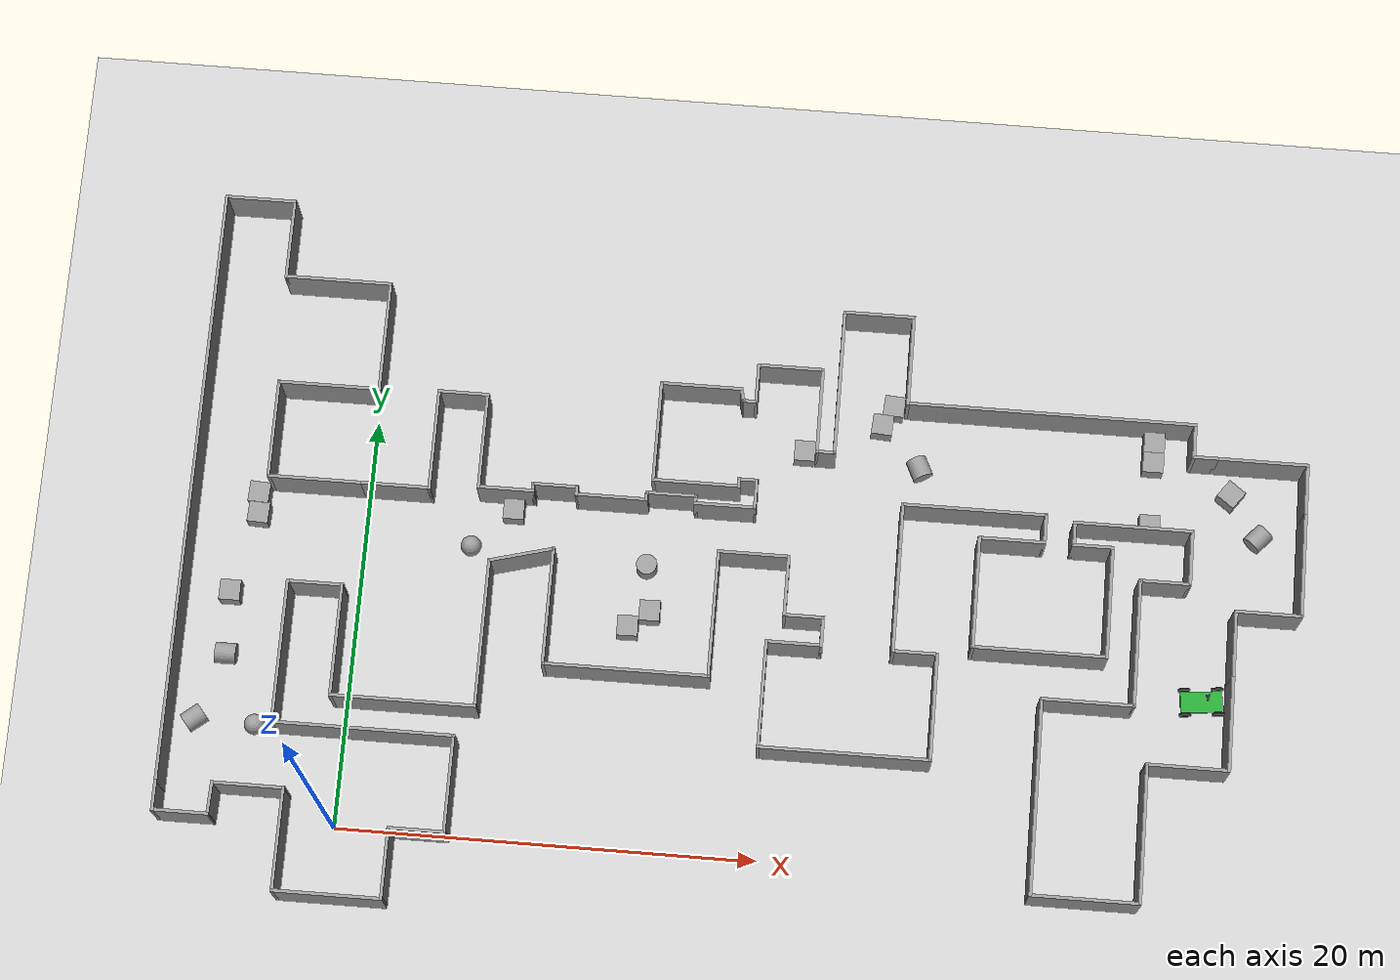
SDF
<sdf version="1.7">
 <world name="default">
  <light name="sun" type="directional">
   <pose>0 0 10 0 -0 0</pose>
   <diffuse>0.8 0.8 0.8 1</diffuse>
   <specular>0.2 0.2 0.2 1</specular>
   <attenuation>
    <range>1000</range>
    <constant>0.9</constant>
    <linear>0.01</linear>
    <quadratic>0.001</quadratic>
   </attenuation>
   <direction>-0.5 0.1 -0.9</direction>
   <spot><inner_angle>0</inner_angle><outer_angle>0</outer_angle><falloff>0</falloff></spot>
  </light>
  <model name="ground_plane">
   <static>1</static>
   <link name="link">
    <collision name="collision">
     <geometry><plane><normal>0 0 1</normal><size>100 100</size></plane></geometry>
     <surface>
      <contact><collide_bitmask>65535</collide_bitmask></contact>
      <friction><ode><mu>100</mu><mu2>50</mu2></ode></friction>
     </surface>
    </collision>
    <visual name="visual">
     <cast_shadows>0</cast_shadows>
     <geometry><plane><normal>0 0 1</normal><size>100 100</size></plane></geometry>
     <material>
      <script><uri>file://media/materials/scripts/gazebo.material</uri><name>Gazebo/Grey</name></script>
     </material>
    </visual>
   </link>
  </model>
  <gravity>0 0 -9.8</gravity>
  <magnetic_field>6e-06 2.3e-05 -4.2e-05</magnetic_field>
  <atmosphere type="adiabatic"/>
  <physics type="ode">
   <max_step_size>0.001</max_step_size>
   <real_time_factor>1</real_time_factor>
   <real_time_update_rate>1000</real_time_update_rate>
  </physics>
  <scene><ambient>0.4 0.4 0.4 1</ambient><background>0.7 0.7 0.7 1</background><shadows>1</shadows></scene>
  <spherical_coordinates>
   <surface_model>EARTH_WGS84</surface_model>
   <latitude_deg>0</latitude_deg>
   <longitude_deg>0</longitude_deg>
   <elevation>0</elevation>
   <heading_deg>0</heading_deg>
  </spherical_coordinates>
  <model name="more_complex_env_0">
   <pose>18.2819 13.3741 0 0 -0 0</pose>
   <link name="Wall_100">
    <collision name="Wall_100_Collision">
     <geometry><box><size>4.5 0.15 2.5</size></box></geometry>
     <pose>0 0 1.25 0 -0 0</pose>
    </collision>
    <visual name="Wall_100_Visual">
     <pose>0 0 1.25 0 -0 0</pose>
     <geometry><box><size>4.5 0.15 2.5</size></box></geometry>
     <material>
      <script><uri>file://media/materials/scripts/gazebo.material</uri><name>Gazebo/Grey</name></script>
      <ambient>1 1 1 1</ambient>
     </material>
     <meta><layer>0</layer></meta>
    </visual>
    <pose>7.29718 11.1773 0 0 -0 -1.5708</pose>
   </link>
   <link name="Wall_101">
    <collision name="Wall_101_Collision">
     <geometry><box><size>14 0.15 2.5</size></box></geometry>
     <pose>0 0 1.25 0 -0 0</pose>
    </collision>
    <visual name="Wall_101_Visual">
     <pose>0 0 1.25 0 -0 0</pose>
     <geometry><box><size>14 0.15 2.5</size></box></geometry>
     <material>
      <script><uri>file://media/materials/scripts/gazebo.material</uri><name>Gazebo/Grey</name></script>
      <ambient>1 1 1 1</ambient>
     </material>
     <meta><layer>0</layer></meta>
    </visual>
    <pose>14.2222 9.00234 0 0 -0 0</pose>
   </link>
   <link name="Wall_102">
    <collision name="Wall_102_Collision">
     <geometry><box><size>1.75 0.15 2.5</size></box></geometry>
     <pose>0 0 1.25 0 -0 0</pose>
    </collision>
    <visual name="Wall_102_Visual">
     <pose>0 0 1.25 0 -0 0</pose>
     <geometry><box><size>1.75 0.15 2.5</size></box></geometry>
     <material>
      <script><uri>file://media/materials/scripts/gazebo.material</uri><name>Gazebo/Grey</name></script>
      <ambient>1 1 1 1</ambient>
     </material>
     <meta><layer>0</layer></meta>
    </visual>
    <pose>21.1472 8.20234 0 0 -0 -1.5708</pose>
   </link>
   <link name="Wall_103">
    <collision name="Wall_103_Collision">
     <geometry><box><size>1.25 0.15 2.5</size></box></geometry>
     <pose>0 0 1.25 0 -0 0</pose>
    </collision>
    <visual name="Wall_103_Visual">
     <pose>0 0 1.25 0 -0 0</pose>
     <geometry><box><size>1.25 0.15 2.5</size></box></geometry>
     <material>
      <script><uri>file://media/materials/scripts/gazebo.material</uri><name>Gazebo/Grey</name></script>
      <ambient>1 1 1 1</ambient>
     </material>
     <meta><layer>0</layer></meta>
    </visual>
    <pose>21.6972 7.40234 0 0 -0 0</pose>
   </link>
   <link name="Wall_104">
    <collision name="Wall_104_Collision">
     <geometry><box><size>4.5 0.15 2.5</size></box></geometry>
     <pose>0 0 1.25 0 -0 0</pose>
    </collision>
    <visual name="Wall_104_Visual">
     <pose>0 0 1.25 0 -0 0</pose>
     <geometry><box><size>4.5 0.15 2.5</size></box></geometry>
     <material>
      <script><uri>file://media/materials/scripts/gazebo.material</uri><name>Gazebo/Grey</name></script>
      <ambient>1 1 1 1</ambient>
     </material>
     <meta><layer>0</layer></meta>
    </visual>
    <pose>24.4222 7.40234 0 0 -0 0</pose>
   </link>
   <link name="Wall_105">
    <collision name="Wall_105_Collision">
     <geometry><box><size>2.5 0.15 2.5</size></box></geometry>
     <pose>0 0 1.25 0 -0 0</pose>
    </collision>
    <visual name="Wall_105_Visual">
     <pose>0 0 1.25 0 -0 0</pose>
     <geometry><box><size>2.5 0.15 2.5</size></box></geometry>
     <material>
      <script><uri>file://media/materials/scripts/gazebo.material</uri><name>Gazebo/Grey</name></script>
      <ambient>1 1 1 1</ambient>
     </material>
     <meta><layer>0</layer></meta>
    </visual>
    <pose>26.5972 6.22734 0 0 -0 -1.5708</pose>
   </link>
   <link name="Wall_106">
    <collision name="Wall_106_Collision">
     <geometry><box><size>5.25 0.15 2.5</size></box></geometry>
     <pose>0 0 1.25 0 -0 0</pose>
    </collision>
    <visual name="Wall_106_Visual">
     <pose>0 0 1.25 0 -0 0</pose>
     <geometry><box><size>5.25 0.15 2.5</size></box></geometry>
     <material>
      <script><uri>file://media/materials/scripts/gazebo.material</uri><name>Gazebo/Grey</name></script>
      <ambient>1 1 1 1</ambient>
     </material>
     <meta><layer>0</layer></meta>
    </visual>
    <pose>26.5972 2.50234 0 0 -0 -1.5708</pose>
   </link>
   <link name="Wall_107">
    <collision name="Wall_107_Collision">
     <geometry><box><size>3.25 0.15 2.5</size></box></geometry>
     <pose>0 0 1.25 0 -0 0</pose>
    </collision>
    <visual name="Wall_107_Visual">
     <pose>0 0 1.25 0 -0 0</pose>
     <geometry><box><size>3.25 0.15 2.5</size></box></geometry>
     <material>
      <script><uri>file://media/materials/scripts/gazebo.material</uri><name>Gazebo/Grey</name></script>
      <ambient>1 1 1 1</ambient>
     </material>
     <meta><layer>0</layer></meta>
    </visual>
    <pose>25.0472 -0.047661 0 0 -0 3.14159</pose>
   </link>
   <link name="Wall_108">
    <collision name="Wall_108_Collision">
     <geometry><box><size>3.25 0.15 2.5</size></box></geometry>
     <pose>0 0 1.25 0 -0 0</pose>
    </collision>
    <visual name="Wall_108_Visual">
     <pose>0 0 1.25 0 -0 0</pose>
     <geometry><box><size>3.25 0.15 2.5</size></box></geometry>
     <material>
      <script><uri>file://media/materials/scripts/gazebo.material</uri><name>Gazebo/Grey</name></script>
      <ambient>1 1 1 1</ambient>
     </material>
     <meta><layer>0</layer></meta>
    </visual>
    <pose>23.4972 -1.59766 0 0 -0 -1.5708</pose>
   </link>
   <link name="Wall_109">
    <collision name="Wall_109_Collision">
     <geometry><box><size>4.75 0.15 2.5</size></box></geometry>
     <pose>0 0 1.25 0 -0 0</pose>
    </collision>
    <visual name="Wall_109_Visual">
     <pose>0 0 1.25 0 -0 0</pose>
     <geometry><box><size>4.75 0.15 2.5</size></box></geometry>
     <material>
      <script><uri>file://media/materials/scripts/gazebo.material</uri><name>Gazebo/Grey</name></script>
      <ambient>1 1 1 1</ambient>
     </material>
     <meta><layer>0</layer></meta>
    </visual>
    <pose>23.4972 -5.44766 0 0 -0 -1.5708</pose>
   </link>
   <link name="Wall_110">
    <collision name="Wall_110_Collision">
     <geometry><box><size>4 0.15 2.5</size></box></geometry>
     <pose>0 0 1.25 0 -0 0</pose>
    </collision>
    <visual name="Wall_110_Visual">
     <pose>0 0 1.25 0 -0 0</pose>
     <geometry><box><size>4 0.15 2.5</size></box></geometry>
     <material>
      <script><uri>file://media/materials/scripts/gazebo.material</uri><name>Gazebo/Grey</name></script>
      <ambient>1 1 1 1</ambient>
     </material>
     <meta><layer>0</layer></meta>
    </visual>
    <pose>21.5722 -7.74766 0 0 -0 3.14159</pose>
   </link>
   <link name="Wall_111">
    <collision name="Wall_111_Collision">
     <geometry><box><size>6.75 0.15 2.5</size></box></geometry>
     <pose>0 0 1.25 0 -0 0</pose>
    </collision>
    <visual name="Wall_111_Visual">
     <pose>0 0 1.25 0 -0 0</pose>
     <geometry><box><size>6.75 0.15 2.5</size></box></geometry>
     <material>
      <script><uri>file://media/materials/scripts/gazebo.material</uri><name>Gazebo/Grey</name></script>
      <ambient>1 1 1 1</ambient>
     </material>
     <meta><layer>0</layer></meta>
    </visual>
    <pose>19.6472 -11.0477 0 0 -0 -1.5708</pose>
   </link>
   <link name="Wall_112">
    <collision name="Wall_112_Collision">
     <geometry><box><size>5.25 0.15 2.5</size></box></geometry>
     <pose>0 0 1.25 0 -0 0</pose>
    </collision>
    <visual name="Wall_112_Visual">
     <pose>0 0 1.25 0 -0 0</pose>
     <geometry><box><size>5.25 0.15 2.5</size></box></geometry>
     <material>
      <script><uri>file://media/materials/scripts/gazebo.material</uri><name>Gazebo/Grey</name></script>
      <ambient>1 1 1 1</ambient>
     </material>
     <meta><layer>0</layer></meta>
    </visual>
    <pose>17.0972 -14.3477 0 0 -0 3.14159</pose>
   </link>
   <link name="Wall_113">
    <collision name="Wall_113_Collision">
     <geometry><box><size>9.5 0.15 2.5</size></box></geometry>
     <pose>0 0 1.25 0 -0 0</pose>
    </collision>
    <visual name="Wall_113_Visual">
     <pose>0 0 1.25 0 -0 0</pose>
     <geometry><box><size>9.5 0.15 2.5</size></box></geometry>
     <material>
      <script><uri>file://media/materials/scripts/gazebo.material</uri><name>Gazebo/Grey</name></script>
      <ambient>1 1 1 1</ambient>
     </material>
     <meta><layer>0</layer></meta>
    </visual>
    <pose>14.5472 -9.67266 0 0 -0 1.5708</pose>
   </link>
   <link name="Wall_114">
    <collision name="Wall_114_Collision">
     <geometry><box><size>4.5 0.15 2.5</size></box></geometry>
     <pose>0 0 1.25 0 -0 0</pose>
    </collision>
    <visual name="Wall_114_Visual">
     <pose>0 0 1.25 0 -0 0</pose>
     <geometry><box><size>4.5 0.15 2.5</size></box></geometry>
     <material>
      <script><uri>file://media/materials/scripts/gazebo.material</uri><name>Gazebo/Grey</name></script>
      <ambient>1 1 1 1</ambient>
     </material>
     <meta><layer>0</layer></meta>
    </visual>
    <pose>16.7222 -4.99766 0 0 -0 0</pose>
   </link>
   <link name="Wall_115">
    <collision name="Wall_115_Collision">
     <geometry><box><size>6.25 0.15 2.5</size></box></geometry>
     <pose>0 0 1.25 0 -0 0</pose>
    </collision>
    <visual name="Wall_115_Visual">
     <pose>0 0 1.25 0 -0 0</pose>
     <geometry><box><size>6.25 0.15 2.5</size></box></geometry>
     <material>
      <script><uri>file://media/materials/scripts/gazebo.material</uri><name>Gazebo/Grey</name></script>
      <ambient>1 1 1 1</ambient>
     </material>
     <meta><layer>0</layer></meta>
    </visual>
    <pose>18.8972 -1.94766 0 0 -0 1.5708</pose>
   </link>
   <link name="Wall_116">
    <collision name="Wall_116_Collision">
     <geometry><box><size>2.5 0.15 2.5</size></box></geometry>
     <pose>0 0 1.25 0 -0 0</pose>
    </collision>
    <visual name="Wall_116_Visual">
     <pose>0 0 1.25 0 -0 0</pose>
     <geometry><box><size>2.5 0.15 2.5</size></box></geometry>
     <material>
      <script><uri>file://media/materials/scripts/gazebo.material</uri><name>Gazebo/Grey</name></script>
      <ambient>1 1 1 1</ambient>
     </material>
     <meta><layer>0</layer></meta>
    </visual>
    <pose>20.0722 1.10234 0 0 -0 0</pose>
   </link>
   <link name="Wall_117">
    <collision name="Wall_117_Collision">
     <geometry><box><size>2.75 0.15 2.5</size></box></geometry>
     <pose>0 0 1.25 0 -0 0</pose>
    </collision>
    <visual name="Wall_117_Visual">
     <pose>0 0 1.25 0 -0 0</pose>
     <geometry><box><size>2.75 0.15 2.5</size></box></geometry>
     <material>
      <script><uri>file://media/materials/scripts/gazebo.material</uri><name>Gazebo/Grey</name></script>
      <ambient>1 1 1 1</ambient>
     </material>
     <meta><layer>0</layer></meta>
    </visual>
    <pose>21.2472 2.40234 0 0 -0 1.5708</pose>
   </link>
   <link name="Wall_118">
    <collision name="Wall_118_Collision">
     <geometry><box><size>5.75 0.15 2.5</size></box></geometry>
     <pose>0 0 1.25 0 -0 0</pose>
    </collision>
    <visual name="Wall_118_Visual">
     <pose>0 0 1.25 0 -0 0</pose>
     <geometry><box><size>5.75 0.15 2.5</size></box></geometry>
     <material>
      <script><uri>file://media/materials/scripts/gazebo.material</uri><name>Gazebo/Grey</name></script>
      <ambient>1 1 1 1</ambient>
     </material>
     <meta><layer>0</layer></meta>
    </visual>
    <pose>18.4472 3.70234 0 0 -0 3.14159</pose>
   </link>
   <link name="Wall_119">
    <collision name="Wall_119_Collision">
     <geometry><box><size>1.25 0.15 2.5</size></box></geometry>
     <pose>0 0 1.25 0 -0 0</pose>
    </collision>
    <visual name="Wall_119_Visual">
     <pose>0 0 1.25 0 -0 0</pose>
     <geometry><box><size>1.25 0.15 2.5</size></box></geometry>
     <material>
      <script><uri>file://media/materials/scripts/gazebo.material</uri><name>Gazebo/Grey</name></script>
      <ambient>1 1 1 1</ambient>
     </material>
     <meta><layer>0</layer></meta>
    </visual>
    <pose>15.6472 3.15234 0 0 -0 -1.5708</pose>
   </link>
   <link name="Wall_120">
    <collision name="Wall_120_Collision">
     <geometry><box><size>2 0.15 2.5</size></box></geometry>
     <pose>0 0 1.25 0 -0 0</pose>
    </collision>
    <visual name="Wall_120_Visual">
     <pose>0 0 1.25 0 -0 0</pose>
     <geometry><box><size>2 0.15 2.5</size></box></geometry>
     <material>
      <script><uri>file://media/materials/scripts/gazebo.material</uri><name>Gazebo/Grey</name></script>
      <ambient>1 1 1 1</ambient>
     </material>
     <meta><layer>0</layer></meta>
    </visual>
    <pose>16.5722 2.60234 0 0 -0 0</pose>
   </link>
   <link name="Wall_121">
    <collision name="Wall_121_Collision">
     <geometry><box><size>5.5 0.15 2.5</size></box></geometry>
     <pose>0 0 1.25 0 -0 0</pose>
    </collision>
    <visual name="Wall_121_Visual">
     <pose>0 0 1.25 0 -0 0</pose>
     <geometry><box><size>5.5 0.15 2.5</size></box></geometry>
     <material>
      <script><uri>file://media/materials/scripts/gazebo.material</uri><name>Gazebo/Grey</name></script>
      <ambient>1 1 1 1</ambient>
     </material>
     <meta><layer>0</layer></meta>
    </visual>
    <pose>17.4972 -0.072661 0 0 -0 -1.5708</pose>
   </link>
   <link name="Wall_122">
    <collision name="Wall_122_Collision">
     <geometry><box><size>6.5 0.15 2.5</size></box></geometry>
     <pose>0 0 1.25 0 -0 0</pose>
    </collision>
    <visual name="Wall_122_Visual">
     <pose>0 0 1.25 0 -0 0</pose>
     <geometry><box><size>6.5 0.15 2.5</size></box></geometry>
     <material>
      <script><uri>file://media/materials/scripts/gazebo.material</uri><name>Gazebo/Grey</name></script>
      <ambient>1 1 1 1</ambient>
     </material>
     <meta><layer>0</layer></meta>
    </visual>
    <pose>14.3222 -2.74766 0 0 -0 3.14159</pose>
   </link>
   <link name="Wall_123">
    <collision name="Wall_123_Collision">
     <geometry><box><size>5.5 0.15 2.5</size></box></geometry>
     <pose>0 0 1.25 0 -0 0</pose>
    </collision>
    <visual name="Wall_123_Visual">
     <pose>0 0 1.25 0 -0 0</pose>
     <geometry><box><size>5.5 0.15 2.5</size></box></geometry>
     <material>
      <script><uri>file://media/materials/scripts/gazebo.material</uri><name>Gazebo/Grey</name></script>
      <ambient>1 1 1 1</ambient>
     </material>
     <meta><layer>0</layer></meta>
    </visual>
    <pose>11.1472 -0.072661 0 0 -0 1.5708</pose>
   </link>
   <link name="Wall_124">
    <collision name="Wall_124_Collision">
     <geometry><box><size>3.25 0.15 2.5</size></box></geometry>
     <pose>0 0 1.25 0 -0 0</pose>
    </collision>
    <visual name="Wall_124_Visual">
     <pose>0 0 1.25 0 -0 0</pose>
     <geometry><box><size>3.25 0.15 2.5</size></box></geometry>
     <material>
      <script><uri>file://media/materials/scripts/gazebo.material</uri><name>Gazebo/Grey</name></script>
      <ambient>1 1 1 1</ambient>
     </material>
     <meta><layer>0</layer></meta>
    </visual>
    <pose>12.6972 2.60234 0 0 -0 0</pose>
   </link>
   <link name="Wall_125">
    <collision name="Wall_125_Collision">
     <geometry><box><size>1.5 0.15 2.5</size></box></geometry>
     <pose>0 0 1.25 0 -0 0</pose>
    </collision>
    <visual name="Wall_125_Visual">
     <pose>0 0 1.25 0 -0 0</pose>
     <geometry><box><size>1.5 0.15 2.5</size></box></geometry>
     <material>
      <script><uri>file://media/materials/scripts/gazebo.material</uri><name>Gazebo/Grey</name></script>
      <ambient>1 1 1 1</ambient>
     </material>
     <meta><layer>0</layer></meta>
    </visual>
    <pose>14.2472 3.27734 0 0 -0 1.5708</pose>
   </link>
   <link name="Wall_126">
    <collision name="Wall_126_Collision">
     <geometry><box><size>7 0.15 2.5</size></box></geometry>
     <pose>0 0 1.25 0 -0 0</pose>
    </collision>
    <visual name="Wall_126_Visual">
     <pose>0 0 1.25 0 -0 0</pose>
     <geometry><box><size>7 0.15 2.5</size></box></geometry>
     <material>
      <script><uri>file://media/materials/scripts/gazebo.material</uri><name>Gazebo/Grey</name></script>
      <ambient>1 1 1 1</ambient>
     </material>
     <meta><layer>0</layer></meta>
    </visual>
    <pose>10.8222 3.95234 0 0 -0 3.14159</pose>
   </link>
   <link name="Wall_127">
    <collision name="Wall_127_Collision">
     <geometry><box><size>2.25 0.15 2.5</size></box></geometry>
     <pose>0 0 1.25 0 -0 0</pose>
    </collision>
    <visual name="Wall_127_Visual">
     <pose>0 0 1.25 0 -0 0</pose>
     <geometry><box><size>2.25 0.15 2.5</size></box></geometry>
     <material>
      <script><uri>file://media/materials/scripts/gazebo.material</uri><name>Gazebo/Grey</name></script>
      <ambient>1 1 1 1</ambient>
     </material>
     <meta><layer>0</layer></meta>
    </visual>
    <pose>7.39719 2.90234 0 0 -0 -1.5708</pose>
   </link>
   <link name="Wall_128">
    <collision name="Wall_128_Collision">
     <geometry><box><size>5.25 0.15 2.5</size></box></geometry>
     <pose>0 0 1.25 0 -0 0</pose>
    </collision>
    <visual name="Wall_128_Visual">
     <pose>0 0 1.25 0 -0 0</pose>
     <geometry><box><size>5.25 0.15 2.5</size></box></geometry>
     <material>
      <script><uri>file://media/materials/scripts/gazebo.material</uri><name>Gazebo/Grey</name></script>
      <ambient>1 1 1 1</ambient>
     </material>
     <meta><layer>0</layer></meta>
    </visual>
    <pose>7.39719 -0.697661 0 0 -0 -1.5708</pose>
   </link>
   <link name="Wall_129">
    <collision name="Wall_129_Collision">
     <geometry><box><size>2.25 0.15 2.5</size></box></geometry>
     <pose>0 0 1.25 0 -0 0</pose>
    </collision>
    <visual name="Wall_129_Visual">
     <pose>0 0 1.25 0 -0 0</pose>
     <geometry><box><size>2.25 0.15 2.5</size></box></geometry>
     <material>
      <script><uri>file://media/materials/scripts/gazebo.material</uri><name>Gazebo/Grey</name></script>
      <ambient>1 1 1 1</ambient>
     </material>
     <meta><layer>0</layer></meta>
    </visual>
    <pose>8.44718 -3.24766 0 0 -0 0</pose>
   </link>
   <link name="Wall_130">
    <collision name="Wall_130_Collision">
     <geometry><box><size>5.25 0.15 2.5</size></box></geometry>
     <pose>0 0 1.25 0 -0 0</pose>
    </collision>
    <visual name="Wall_130_Visual">
     <pose>0 0 1.25 0 -0 0</pose>
     <geometry><box><size>5.25 0.15 2.5</size></box></geometry>
     <material>
      <script><uri>file://media/materials/scripts/gazebo.material</uri><name>Gazebo/Grey</name></script>
      <ambient>1 1 1 1</ambient>
     </material>
     <meta><layer>0</layer></meta>
    </visual>
    <pose>9.49718 -5.79766 0 0 -0 -1.5708</pose>
   </link>
   <link name="Wall_131">
    <collision name="Wall_131_Collision">
     <geometry><box><size>8.25 0.15 2.5</size></box></geometry>
     <pose>0 0 1.25 0 -0 0</pose>
    </collision>
    <visual name="Wall_131_Visual">
     <pose>0 0 1.25 0 -0 0</pose>
     <geometry><box><size>8.25 0.15 2.5</size></box></geometry>
     <material>
      <script><uri>file://media/materials/scripts/gazebo.material</uri><name>Gazebo/Grey</name></script>
      <ambient>1 1 1 1</ambient>
     </material>
     <meta><layer>0</layer></meta>
    </visual>
    <pose>5.44719 -8.34766 0 0 -0 3.14159</pose>
   </link>
   <link name="Wall_132">
    <collision name="Wall_132_Collision">
     <geometry><box><size>5.25 0.15 2.5</size></box></geometry>
     <pose>0 0 1.25 0 -0 0</pose>
    </collision>
    <visual name="Wall_132_Visual">
     <pose>0 0 1.25 0 -0 0</pose>
     <geometry><box><size>5.25 0.15 2.5</size></box></geometry>
     <material>
      <script><uri>file://media/materials/scripts/gazebo.material</uri><name>Gazebo/Grey</name></script>
      <ambient>1 1 1 1</ambient>
     </material>
     <meta><layer>0</layer></meta>
    </visual>
    <pose>1.39718 -5.79766 0 0 -0 1.5708</pose>
   </link>
   <link name="Wall_133">
    <collision name="Wall_133_Collision">
     <geometry><box><size>2.75 0.15 2.5</size></box></geometry>
     <pose>0 0 1.25 0 -0 0</pose>
    </collision>
    <visual name="Wall_133_Visual">
     <pose>0 0 1.25 0 -0 0</pose>
     <geometry><box><size>2.75 0.15 2.5</size></box></geometry>
     <material>
      <script><uri>file://media/materials/scripts/gazebo.material</uri><name>Gazebo/Grey</name></script>
      <ambient>1 1 1 1</ambient>
     </material>
     <meta><layer>0</layer></meta>
    </visual>
    <pose>2.69719 -3.24766 0 0 -0 0</pose>
   </link>
   <link name="Wall_134">
    <collision name="Wall_134_Collision">
     <geometry><box><size>1.5 0.15 2.5</size></box></geometry>
     <pose>0 0 1.25 0 -0 0</pose>
    </collision>
    <visual name="Wall_134_Visual">
     <pose>0 0 1.25 0 -0 0</pose>
     <geometry><box><size>1.5 0.15 2.5</size></box></geometry>
     <material>
      <script><uri>file://media/materials/scripts/gazebo.material</uri><name>Gazebo/Grey</name></script>
      <ambient>1 1 1 1</ambient>
     </material>
     <meta><layer>0</layer></meta>
    </visual>
    <pose>3.99718 -2.57266 0 0 -0 1.5708</pose>
   </link>
   <link name="Wall_135">
    <collision name="Wall_135_Collision">
     <geometry><box><size>2 0.15 2.5</size></box></geometry>
     <pose>0 0 1.25 0 -0 0</pose>
    </collision>
    <visual name="Wall_135_Visual">
     <pose>0 0 1.25 0 -0 0</pose>
     <geometry><box><size>2 0.15 2.5</size></box></geometry>
     <material>
      <script><uri>file://media/materials/scripts/gazebo.material</uri><name>Gazebo/Grey</name></script>
      <ambient>1 1 1 1</ambient>
     </material>
     <meta><layer>0</layer></meta>
    </visual>
    <pose>3.07219 -1.89766 0 0 -0 3.14159</pose>
   </link>
   <link name="Wall_136">
    <collision name="Wall_136_Collision">
     <geometry><box><size>3 0.15 2.5</size></box></geometry>
     <pose>0 0 1.25 0 -0 0</pose>
    </collision>
    <visual name="Wall_136_Visual">
     <pose>0 0 1.25 0 -0 0</pose>
     <geometry><box><size>3 0.15 2.5</size></box></geometry>
     <material>
      <script><uri>file://media/materials/scripts/gazebo.material</uri><name>Gazebo/Grey</name></script>
      <ambient>1 1 1 1</ambient>
     </material>
     <meta><layer>0</layer></meta>
    </visual>
    <pose>2.14718 -0.472661 0 0 -0 1.5708</pose>
   </link>
   <link name="Wall_137">
    <collision name="Wall_137_Collision">
     <geometry><box><size>3.5 0.15 2.5</size></box></geometry>
     <pose>0 0 1.25 0 -0 0</pose>
    </collision>
    <visual name="Wall_137_Visual">
     <pose>0 0 1.25 0 -0 0</pose>
     <geometry><box><size>3.5 0.15 2.5</size></box></geometry>
     <material>
      <script><uri>file://media/materials/scripts/gazebo.material</uri><name>Gazebo/Grey</name></script>
      <ambient>1 1 1 1</ambient>
     </material>
     <meta><layer>0</layer></meta>
    </visual>
    <pose>0.472185 0.952339 0 0 -0 3.14159</pose>
   </link>
   <link name="Wall_138">
    <collision name="Wall_138_Collision">
     <geometry><box><size>6.25 0.15 2.5</size></box></geometry>
     <pose>0 0 1.25 0 -0 0</pose>
    </collision>
    <visual name="Wall_138_Visual">
     <pose>0 0 1.25 0 -0 0</pose>
     <geometry><box><size>6.25 0.15 2.5</size></box></geometry>
     <material>
      <script><uri>file://media/materials/scripts/gazebo.material</uri><name>Gazebo/Grey</name></script>
      <ambient>1 1 1 1</ambient>
     </material>
     <meta><layer>0</layer></meta>
    </visual>
    <pose>-1.20281 -2.09766 0 0 -0 -1.5708</pose>
   </link>
   <link name="Wall_139">
    <collision name="Wall_139_Collision">
     <geometry><box><size>8 0.15 2.5</size></box></geometry>
     <pose>0 0 1.25 0 -0 0</pose>
    </collision>
    <visual name="Wall_139_Visual">
     <pose>0 0 1.25 0 -0 0</pose>
     <geometry><box><size>8 0.15 2.5</size></box></geometry>
     <material>
      <script><uri>file://media/materials/scripts/gazebo.material</uri><name>Gazebo/Grey</name></script>
      <ambient>1 1 1 1</ambient>
     </material>
     <meta><layer>0</layer></meta>
    </visual>
    <pose>-5.12782 -5.14766 0 0 -0 3.14159</pose>
   </link>
   <link name="Wall_140">
    <collision name="Wall_140_Collision">
     <geometry><box><size>5.75 0.15 2.5</size></box></geometry>
     <pose>0 0 1.25 0 -0 0</pose>
    </collision>
    <visual name="Wall_140_Visual">
     <pose>0 0 1.25 0 -0 0</pose>
     <geometry><box><size>5.75 0.15 2.5</size></box></geometry>
     <material>
      <script><uri>file://media/materials/scripts/gazebo.material</uri><name>Gazebo/Grey</name></script>
      <ambient>1 1 1 1</ambient>
     </material>
     <meta><layer>0</layer></meta>
    </visual>
    <pose>-9.05281 -2.34766 0 0 -0 1.5708</pose>
   </link>
   <link name="Wall_141">
    <collision name="Wall_141_Collision">
     <geometry><box><size>3.25 0.15 2.5</size></box></geometry>
     <pose>0 0 1.25 0 -0 0</pose>
    </collision>
    <visual name="Wall_141_Visual">
     <pose>0 0 1.25 0 -0 0</pose>
     <geometry><box><size>3.25 0.15 2.5</size></box></geometry>
     <material>
      <script><uri>file://media/materials/scripts/gazebo.material</uri><name>Gazebo/Grey</name></script>
      <ambient>1 1 1 1</ambient>
     </material>
     <meta><layer>0</layer></meta>
    </visual>
    <pose>-10.55 0.051169 0 0 -0 -2.87979</pose>
   </link>
   <link name="Wall_142">
    <collision name="Wall_142_Collision">
     <geometry><box><size>7.25 0.15 2.5</size></box></geometry>
     <pose>0 0 1.25 0 -0 0</pose>
    </collision>
    <visual name="Wall_142_Visual">
     <pose>0 0 1.25 0 -0 0</pose>
     <geometry><box><size>7.25 0.15 2.5</size></box></geometry>
     <material>
      <script><uri>file://media/materials/scripts/gazebo.material</uri><name>Gazebo/Grey</name></script>
      <ambient>1 1 1 1</ambient>
     </material>
     <meta><layer>0</layer></meta>
    </visual>
    <pose>-12.0472 -3.9 0 0 -0 -1.5708</pose>
   </link>
   <link name="Wall_143">
    <collision name="Wall_143_Collision">
     <geometry><box><size>7 0.15 2.5</size></box></geometry>
     <pose>0 0 1.25 0 -0 0</pose>
    </collision>
    <visual name="Wall_143_Visual">
     <pose>0 0 1.25 0 -0 0</pose>
     <geometry><box><size>7 0.15 2.5</size></box></geometry>
     <material>
      <script><uri>file://media/materials/scripts/gazebo.material</uri><name>Gazebo/Grey</name></script>
      <ambient>1 1 1 1</ambient>
     </material>
     <meta><layer>0</layer></meta>
    </visual>
    <pose>-15.4722 -7.45 0 0 -0 3.14159</pose>
   </link>
   <link name="Wall_144">
    <collision name="Wall_144_Collision">
     <geometry><box><size>5.5 0.15 2.5</size></box></geometry>
     <pose>0 0 1.25 0 -0 0</pose>
    </collision>
    <visual name="Wall_144_Visual">
     <pose>0 0 1.25 0 -0 0</pose>
     <geometry><box><size>5.5 0.15 2.5</size></box></geometry>
     <material>
      <script><uri>file://media/materials/scripts/gazebo.material</uri><name>Gazebo/Grey</name></script>
      <ambient>1 1 1 1</ambient>
     </material>
     <meta><layer>0</layer></meta>
    </visual>
    <pose>-18.8972 -4.775 0 0 -0 1.5708</pose>
   </link>
   <link name="Wall_145">
    <collision name="Wall_145_Collision">
     <geometry><box><size>2.75 0.15 2.5</size></box></geometry>
     <pose>0 0 1.25 0 -0 0</pose>
    </collision>
    <visual name="Wall_145_Visual">
     <pose>0 0 1.25 0 -0 0</pose>
     <geometry><box><size>2.75 0.15 2.5</size></box></geometry>
     <material>
      <script><uri>file://media/materials/scripts/gazebo.material</uri><name>Gazebo/Grey</name></script>
      <ambient>1 1 1 1</ambient>
     </material>
     <meta><layer>0</layer></meta>
    </visual>
    <pose>-20.1972 -2.1 0 0 -0 3.14159</pose>
   </link>
   <link name="Wall_148">
    <collision name="Wall_148_Collision">
     <geometry><box><size>29.25 0.15 2.5</size></box></geometry>
     <pose>0 0 1.25 0 -0 0</pose>
    </collision>
    <visual name="Wall_148_Visual">
     <pose>0 0 1.25 0 -0 0</pose>
     <geometry><box><size>29.25 0.15 2.5</size></box></geometry>
     <material>
      <script><uri>file://media/materials/scripts/gazebo.material</uri><name>Gazebo/Grey</name></script>
      <ambient>1 1 1 1</ambient>
     </material>
     <meta><layer>0</layer></meta>
    </visual>
    <pose>-26.5972 2.35 0 0 -0 1.5708</pose>
   </link>
   <link name="Wall_149">
    <collision name="Wall_149_Collision">
     <geometry><box><size>3.5 0.15 2.5</size></box></geometry>
     <pose>0 0 1.25 0 -0 0</pose>
    </collision>
    <visual name="Wall_149_Visual">
     <pose>0 0 1.25 0 -0 0</pose>
     <geometry><box><size>3.5 0.15 2.5</size></box></geometry>
     <material>
      <script><uri>file://media/materials/scripts/gazebo.material</uri><name>Gazebo/Grey</name></script>
      <ambient>1 1 1 1</ambient>
     </material>
     <meta><layer>0</layer></meta>
    </visual>
    <pose>-24.9222 16.9 0 0 -0 0</pose>
   </link>
   <link name="Wall_150">
    <collision name="Wall_150_Collision">
     <geometry><box><size>4 0.15 2.5</size></box></geometry>
     <pose>0 0 1.25 0 -0 0</pose>
    </collision>
    <visual name="Wall_150_Visual">
     <pose>0 0 1.25 0 -0 0</pose>
     <geometry><box><size>4 0.15 2.5</size></box></geometry>
     <material>
      <script><uri>file://media/materials/scripts/gazebo.material</uri><name>Gazebo/Grey</name></script>
      <ambient>1 1 1 1</ambient>
     </material>
     <meta><layer>0</layer></meta>
    </visual>
    <pose>-23.2472 14.975 0 0 -0 -1.5708</pose>
   </link>
   <link name="Wall_151">
    <collision name="Wall_151_Collision">
     <geometry><box><size>5.25 0.15 2.5</size></box></geometry>
     <pose>0 0 1.25 0 -0 0</pose>
    </collision>
    <visual name="Wall_151_Visual">
     <pose>0 0 1.25 0 -0 0</pose>
     <geometry><box><size>5.25 0.15 2.5</size></box></geometry>
     <material>
      <script><uri>file://media/materials/scripts/gazebo.material</uri><name>Gazebo/Grey</name></script>
      <ambient>1 1 1 1</ambient>
     </material>
     <meta><layer>0</layer></meta>
    </visual>
    <pose>-20.6972 13.05 0 0 -0 0</pose>
   </link>
   <link name="Wall_152">
    <collision name="Wall_152_Collision">
     <geometry><box><size>5.5 0.15 2.5</size></box></geometry>
     <pose>0 0 1.25 0 -0 0</pose>
    </collision>
    <visual name="Wall_152_Visual">
     <pose>0 0 1.25 0 -0 0</pose>
     <geometry><box><size>5.5 0.15 2.5</size></box></geometry>
     <material>
      <script><uri>file://media/materials/scripts/gazebo.material</uri><name>Gazebo/Grey</name></script>
      <ambient>1 1 1 1</ambient>
     </material>
     <meta><layer>0</layer></meta>
    </visual>
    <pose>-18.1472 10.375 0 0 -0 -1.5708</pose>
   </link>
   <link name="Wall_153">
    <collision name="Wall_153_Collision">
     <geometry><box><size>5 0.15 2.5</size></box></geometry>
     <pose>0 0 1.25 0 -0 0</pose>
    </collision>
    <visual name="Wall_153_Visual">
     <pose>0 0 1.25 0 -0 0</pose>
     <geometry><box><size>5 0.15 2.5</size></box></geometry>
     <material>
      <script><uri>file://media/materials/scripts/gazebo.material</uri><name>Gazebo/Grey</name></script>
      <ambient>1 1 1 1</ambient>
     </material>
     <meta><layer>0</layer></meta>
    </visual>
    <pose>-20.5722 7.7 0 0 -0 3.14159</pose>
   </link>
   <link name="Wall_154">
    <collision name="Wall_154_Collision">
     <geometry><box><size>4.75 0.15 2.5</size></box></geometry>
     <pose>0 0 1.25 0 -0 0</pose>
    </collision>
    <visual name="Wall_154_Visual">
     <pose>0 0 1.25 0 -0 0</pose>
     <geometry><box><size>4.75 0.15 2.5</size></box></geometry>
     <material>
      <script><uri>file://media/materials/scripts/gazebo.material</uri><name>Gazebo/Grey</name></script>
      <ambient>1 1 1 1</ambient>
     </material>
     <meta><layer>0</layer></meta>
    </visual>
    <pose>-22.9972 5.4 0 0 -0 -1.5708</pose>
   </link>
   <link name="Wall_157">
    <collision name="Wall_157_Collision">
     <geometry><box><size>4.5 0.15 2.5</size></box></geometry>
     <pose>0 0 1.25 0 -0 0</pose>
    </collision>
    <visual name="Wall_157_Visual">
     <pose>0 0 1.25 0 -0 0</pose>
     <geometry><box><size>4.5 0.15 2.5</size></box></geometry>
     <material>
      <script><uri>file://media/materials/scripts/gazebo.material</uri><name>Gazebo/Grey</name></script>
      <ambient>1 1 1 1</ambient>
     </material>
     <meta><layer>0</layer></meta>
    </visual>
    <pose>-20.7831 2.98189 0 0 -0 3.14159</pose>
   </link>
   <link name="Wall_158">
    <collision name="Wall_158_Collision">
     <geometry><box><size>0.15 0.15 2.5</size></box></geometry>
     <pose>0 0 1.25 0 -0 0</pose>
    </collision>
    <visual name="Wall_158_Visual">
     <pose>0 0 1.25 0 -0 0</pose>
     <geometry><box><size>0.15 0.15 2.5</size></box></geometry>
     <material>
      <script><uri>file://media/materials/scripts/gazebo.material</uri><name>Gazebo/Grey</name></script>
      <ambient>1 1 1 1</ambient>
     </material>
     <meta><layer>0</layer></meta>
    </visual>
    <pose>-22.9581 2.98189 0 0 -0 0</pose>
   </link>
   <link name="Wall_160">
    <collision name="Wall_160_Collision">
     <geometry><box><size>7 0.15 2.5</size></box></geometry>
     <pose>0 0 1.25 0 -0 0</pose>
    </collision>
    <visual name="Wall_160_Visual">
     <pose>0 0 1.25 0 -0 0</pose>
     <geometry><box><size>7 0.15 2.5</size></box></geometry>
     <material>
      <script><uri>file://media/materials/scripts/gazebo.material</uri><name>Gazebo/Grey</name></script>
      <ambient>1 1 1 1</ambient>
     </material>
     <meta><layer>0</layer></meta>
    </visual>
    <pose>-21.4972 -5.525 0 0 -0 -1.5708</pose>
   </link>
   <link name="Wall_161">
    <collision name="Wall_161_Collision">
     <geometry><box><size>8.75 0.15 2.5</size></box></geometry>
     <pose>0 0 1.25 0 -0 0</pose>
    </collision>
    <visual name="Wall_161_Visual">
     <pose>0 0 1.25 0 -0 0</pose>
     <geometry><box><size>8.75 0.15 2.5</size></box></geometry>
     <material>
      <script><uri>file://media/materials/scripts/gazebo.material</uri><name>Gazebo/Grey</name></script>
      <ambient>1 1 1 1</ambient>
     </material>
     <meta><layer>0</layer></meta>
    </visual>
    <pose>-17.1972 -8.95 0 0 -0 0</pose>
   </link>
   <link name="Wall_162">
    <collision name="Wall_162_Collision">
     <geometry><box><size>4.75 0.15 2.5</size></box></geometry>
     <pose>0 0 1.25 0 -0 0</pose>
    </collision>
    <visual name="Wall_162_Visual">
     <pose>0 0 1.25 0 -0 0</pose>
     <geometry><box><size>4.75 0.15 2.5</size></box></geometry>
     <material>
      <script><uri>file://media/materials/scripts/gazebo.material</uri><name>Gazebo/Grey</name></script>
      <ambient>1 1 1 1</ambient>
     </material>
     <meta><layer>0</layer></meta>
    </visual>
    <pose>-12.8972 -11.25 0 0 -0 -1.5708</pose>
   </link>
   <link name="Wall_163">
    <collision name="Wall_163_Collision">
     <geometry><box><size>2.75 0.15 2.5</size></box></geometry>
     <pose>0 0 1.25 0 -0 0</pose>
    </collision>
    <visual name="Wall_163_Visual">
     <pose>0 0 1.25 0 -0 0</pose>
     <geometry><box><size>2.75 0.15 2.5</size></box></geometry>
     <material>
      <script><uri>file://media/materials/scripts/gazebo.material</uri><name>Gazebo/Grey</name></script>
      <ambient>1 1 1 1</ambient>
     </material>
     <meta><layer>0</layer></meta>
    </visual>
    <pose>-14.1972 -13.55 0 0 -0 3.14159</pose>
   </link>
   <link name="Wall_164">
    <collision name="Wall_164_Collision">
     <geometry><box><size>3.5 0.15 2.5</size></box></geometry>
     <pose>0 0 1.25 0 -0 0</pose>
    </collision>
    <visual name="Wall_164_Visual">
     <pose>0 0 1.25 0 -0 0</pose>
     <geometry><box><size>3.5 0.15 2.5</size></box></geometry>
     <material>
      <script><uri>file://media/materials/scripts/gazebo.material</uri><name>Gazebo/Grey</name></script>
      <ambient>1 1 1 1</ambient>
     </material>
     <meta><layer>0</layer></meta>
    </visual>
    <pose>-15.4972 -15.225 0 0 -0 -1.5708</pose>
   </link>
   <link name="Wall_165">
    <collision name="Wall_165_Collision">
     <geometry><box><size>5.25 0.15 2.5</size></box></geometry>
     <pose>0 0 1.25 0 -0 0</pose>
    </collision>
    <visual name="Wall_165_Visual">
     <pose>0 0 1.25 0 -0 0</pose>
     <geometry><box><size>5.25 0.15 2.5</size></box></geometry>
     <material>
      <script><uri>file://media/materials/scripts/gazebo.material</uri><name>Gazebo/Grey</name></script>
      <ambient>1 1 1 1</ambient>
     </material>
     <meta><layer>0</layer></meta>
    </visual>
    <pose>-18.0472 -16.9 0 0 -0 3.14159</pose>
   </link>
   <link name="Wall_166">
    <collision name="Wall_166_Collision">
     <geometry><box><size>5 0.15 2.5</size></box></geometry>
     <pose>0 0 1.25 0 -0 0</pose>
    </collision>
    <visual name="Wall_166_Visual">
     <pose>0 0 1.25 0 -0 0</pose>
     <geometry><box><size>5 0.15 2.5</size></box></geometry>
     <material>
      <script><uri>file://media/materials/scripts/gazebo.material</uri><name>Gazebo/Grey</name></script>
      <ambient>1 1 1 1</ambient>
     </material>
     <meta><layer>0</layer></meta>
    </visual>
    <pose>-20.5972 -14.475 0 0 -0 1.5708</pose>
   </link>
   <link name="Wall_167">
    <collision name="Wall_167_Collision">
     <geometry><box><size>3.5 0.15 2.5</size></box></geometry>
     <pose>0 0 1.25 0 -0 0</pose>
    </collision>
    <visual name="Wall_167_Visual">
     <pose>0 0 1.25 0 -0 0</pose>
     <geometry><box><size>3.5 0.15 2.5</size></box></geometry>
     <material>
      <script><uri>file://media/materials/scripts/gazebo.material</uri><name>Gazebo/Grey</name></script>
      <ambient>1 1 1 1</ambient>
     </material>
     <meta><layer>0</layer></meta>
    </visual>
    <pose>-22.2722 -12.05 0 0 -0 3.14159</pose>
   </link>
   <link name="Wall_172">
    <collision name="Wall_172_Collision">
     <geometry><box><size>1.5 0.15 2.5</size></box></geometry>
     <pose>0 0 1.25 0 -0 0</pose>
    </collision>
    <visual name="Wall_172_Visual">
     <pose>0 0 1.25 0 -0 0</pose>
     <geometry><box><size>1.5 0.15 2.5</size></box></geometry>
     <material>
      <script><uri>file://media/materials/scripts/gazebo.material</uri><name>Gazebo/Grey</name></script>
      <ambient>1 1 1 1</ambient>
     </material>
     <meta><layer>0</layer></meta>
    </visual>
    <pose>-26.5972 -12.875 0 0 -0 -1.5708</pose>
   </link>
   <link name="Wall_173">
    <collision name="Wall_173_Collision">
     <geometry><box><size>2.75 0.15 2.5</size></box></geometry>
     <pose>0 0 1.25 0 -0 0</pose>
    </collision>
    <visual name="Wall_173_Visual">
     <pose>0 0 1.25 0 -0 0</pose>
     <geometry><box><size>2.75 0.15 2.5</size></box></geometry>
     <material>
      <script><uri>file://media/materials/scripts/gazebo.material</uri><name>Gazebo/Grey</name></script>
      <ambient>1 1 1 1</ambient>
     </material>
     <meta><layer>0</layer></meta>
    </visual>
    <pose>-25.2972 -13.55 0 0 -0 0</pose>
   </link>
   <link name="Wall_177">
    <collision name="Wall_177_Collision">
     <geometry><box><size>1.65083 0.15 2.5</size></box></geometry>
     <pose>0 0 1.25 0 -0 0</pose>
    </collision>
    <visual name="Wall_177_Visual">
     <pose>0 0 1.25 0 -0 0</pose>
     <geometry><box><size>1.65083 0.15 2.5</size></box></geometry>
     <material>
      <script><uri>file://media/materials/scripts/gazebo.material</uri><name>Gazebo/Grey</name></script>
      <ambient>1 1 1 1</ambient>
     </material>
     <meta><layer>0</layer></meta>
    </visual>
    <pose>-23.9722 -12.8 0 0 -0 -1.60412</pose>
   </link>
   <link name="Wall_73">
    <collision name="Wall_73_Collision">
     <geometry><box><size>3.5 0.15 2.5</size></box></geometry>
     <pose>0 0 1.25 0 -0 0</pose>
    </collision>
    <visual name="Wall_73_Visual">
     <pose>0 0 1.25 0 -0 0</pose>
     <geometry><box><size>3.5 0.15 2.5</size></box></geometry>
     <material>
      <script><uri>file://media/materials/scripts/gazebo.material</uri><name>Gazebo/Grey</name></script>
      <ambient>1 1 1 1</ambient>
     </material>
     <meta><layer>0</layer></meta>
    </visual>
    <pose>-16.9331 2.98189 0 0 -0 0</pose>
   </link>
   <link name="Wall_74">
    <collision name="Wall_74_Collision">
     <geometry><box><size>5 0.15 2.5</size></box></geometry>
     <pose>0 0 1.25 0 -0 0</pose>
    </collision>
    <visual name="Wall_74_Visual">
     <pose>0 0 1.25 0 -0 0</pose>
     <geometry><box><size>5 0.15 2.5</size></box></geometry>
     <material>
      <script><uri>file://media/materials/scripts/gazebo.material</uri><name>Gazebo/Grey</name></script>
      <ambient>1 1 1 1</ambient>
     </material>
     <meta><layer>0</layer></meta>
    </visual>
    <pose>-15.2581 5.40689 0 0 -0 1.5708</pose>
   </link>
   <link name="Wall_75">
    <collision name="Wall_75_Collision">
     <geometry><box><size>2.5 0.15 2.5</size></box></geometry>
     <pose>0 0 1.25 0 -0 0</pose>
    </collision>
    <visual name="Wall_75_Visual">
     <pose>0 0 1.25 0 -0 0</pose>
     <geometry><box><size>2.5 0.15 2.5</size></box></geometry>
     <material>
      <script><uri>file://media/materials/scripts/gazebo.material</uri><name>Gazebo/Grey</name></script>
      <ambient>1 1 1 1</ambient>
     </material>
     <meta><layer>0</layer></meta>
    </visual>
    <pose>-14.0831 7.83189 0 0 -0 0</pose>
   </link>
   <link name="Wall_76">
    <collision name="Wall_76_Collision">
     <geometry><box><size>4.75 0.15 2.5</size></box></geometry>
     <pose>0 0 1.25 0 -0 0</pose>
    </collision>
    <visual name="Wall_76_Visual">
     <pose>0 0 1.25 0 -0 0</pose>
     <geometry><box><size>4.75 0.15 2.5</size></box></geometry>
     <material>
      <script><uri>file://media/materials/scripts/gazebo.material</uri><name>Gazebo/Grey</name></script>
      <ambient>1 1 1 1</ambient>
     </material>
     <meta><layer>0</layer></meta>
    </visual>
    <pose>-12.9081 5.53189 0 0 -0 -1.5708</pose>
   </link>
   <link name="Wall_77">
    <collision name="Wall_77_Collision">
     <geometry><box><size>2.75 0.15 2.5</size></box></geometry>
     <pose>0 0 1.25 0 -0 0</pose>
    </collision>
    <visual name="Wall_77_Visual">
     <pose>0 0 1.25 0 -0 0</pose>
     <geometry><box><size>2.75 0.15 2.5</size></box></geometry>
     <material>
      <script><uri>file://media/materials/scripts/gazebo.material</uri><name>Gazebo/Grey</name></script>
      <ambient>1 1 1 1</ambient>
     </material>
     <meta><layer>0</layer></meta>
    </visual>
    <pose>-11.6081 3.23189 0 0 -0 0</pose>
   </link>
   <link name="Wall_78">
    <collision name="Wall_78_Collision">
     <geometry><box><size>0.5 0.15 2.5</size></box></geometry>
     <pose>0 0 1.25 0 -0 0</pose>
    </collision>
    <visual name="Wall_78_Visual">
     <pose>0 0 1.25 0 -0 0</pose>
     <geometry><box><size>0.5 0.15 2.5</size></box></geometry>
     <material>
      <script><uri>file://media/materials/scripts/gazebo.material</uri><name>Gazebo/Grey</name></script>
      <ambient>1 1 1 1</ambient>
     </material>
     <meta><layer>0</layer></meta>
    </visual>
    <pose>-10.3081 3.40689 0 0 -0 1.5708</pose>
   </link>
   <link name="Wall_79">
    <collision name="Wall_79_Collision">
     <geometry><box><size>2.25 0.15 2.5</size></box></geometry>
     <pose>0 0 1.25 0 -0 0</pose>
    </collision>
    <visual name="Wall_79_Visual">
     <pose>0 0 1.25 0 -0 0</pose>
     <geometry><box><size>2.25 0.15 2.5</size></box></geometry>
     <material>
      <script><uri>file://media/materials/scripts/gazebo.material</uri><name>Gazebo/Grey</name></script>
      <ambient>1 1 1 1</ambient>
     </material>
     <meta><layer>0</layer></meta>
    </visual>
    <pose>-9.25811 3.58189 0 0 -0 0</pose>
   </link>
   <link name="Wall_80">
    <collision name="Wall_80_Collision">
     <geometry><box><size>0.5 0.15 2.5</size></box></geometry>
     <pose>0 0 1.25 0 -0 0</pose>
    </collision>
    <visual name="Wall_80_Visual">
     <pose>0 0 1.25 0 -0 0</pose>
     <geometry><box><size>0.5 0.15 2.5</size></box></geometry>
     <material>
      <script><uri>file://media/materials/scripts/gazebo.material</uri><name>Gazebo/Grey</name></script>
      <ambient>1 1 1 1</ambient>
     </material>
     <meta><layer>0</layer></meta>
    </visual>
    <pose>-8.20811 3.40689 0 0 -0 -1.5708</pose>
   </link>
   <link name="Wall_81">
    <collision name="Wall_81_Collision">
     <geometry><box><size>3.5 0.15 2.5</size></box></geometry>
     <pose>0 0 1.25 0 -0 0</pose>
    </collision>
    <visual name="Wall_81_Visual">
     <pose>0 0 1.25 0 -0 0</pose>
     <geometry><box><size>3.5 0.15 2.5</size></box></geometry>
     <material>
      <script><uri>file://media/materials/scripts/gazebo.material</uri><name>Gazebo/Grey</name></script>
      <ambient>1 1 1 1</ambient>
     </material>
     <meta><layer>0</layer></meta>
    </visual>
    <pose>-6.53311 3.23189 0 0 -0 0</pose>
   </link>
   <link name="Wall_82">
    <collision name="Wall_82_Collision">
     <geometry><box><size>0.5 0.15 2.5</size></box></geometry>
     <pose>0 0 1.25 0 -0 0</pose>
    </collision>
    <visual name="Wall_82_Visual">
     <pose>0 0 1.25 0 -0 0</pose>
     <geometry><box><size>0.5 0.15 2.5</size></box></geometry>
     <material>
      <script><uri>file://media/materials/scripts/gazebo.material</uri><name>Gazebo/Grey</name></script>
      <ambient>1 1 1 1</ambient>
     </material>
     <meta><layer>0</layer></meta>
    </visual>
    <pose>-4.85811 3.40689 0 0 -0 1.5708</pose>
   </link>
   <link name="Wall_83">
    <collision name="Wall_83_Collision">
     <geometry><box><size>2.5 0.15 2.5</size></box></geometry>
     <pose>0 0 1.25 0 -0 0</pose>
    </collision>
    <visual name="Wall_83_Visual">
     <pose>0 0 1.25 0 -0 0</pose>
     <geometry><box><size>2.5 0.15 2.5</size></box></geometry>
     <material>
      <script><uri>file://media/materials/scripts/gazebo.material</uri><name>Gazebo/Grey</name></script>
      <ambient>1 1 1 1</ambient>
     </material>
     <meta><layer>0</layer></meta>
    </visual>
    <pose>-3.68311 3.58189 0 0 -0 0</pose>
   </link>
   <link name="Wall_84">
    <collision name="Wall_84_Collision">
     <geometry><box><size>0.5 0.15 2.5</size></box></geometry>
     <pose>0 0 1.25 0 -0 0</pose>
    </collision>
    <visual name="Wall_84_Visual">
     <pose>0 0 1.25 0 -0 0</pose>
     <geometry><box><size>0.5 0.15 2.5</size></box></geometry>
     <material>
      <script><uri>file://media/materials/scripts/gazebo.material</uri><name>Gazebo/Grey</name></script>
      <ambient>1 1 1 1</ambient>
     </material>
     <meta><layer>0</layer></meta>
    </visual>
    <pose>-2.50811 3.40689 0 0 -0 -1.5708</pose>
   </link>
   <link name="Wall_85">
    <collision name="Wall_85_Collision">
     <geometry><box><size>3 0.15 2.5</size></box></geometry>
     <pose>0 0 1.25 0 -0 0</pose>
    </collision>
    <visual name="Wall_85_Visual">
     <pose>0 0 1.25 0 -0 0</pose>
     <geometry><box><size>3 0.15 2.5</size></box></geometry>
     <material>
      <script><uri>file://media/materials/scripts/gazebo.material</uri><name>Gazebo/Grey</name></script>
      <ambient>1 1 1 1</ambient>
     </material>
     <meta><layer>0</layer></meta>
    </visual>
    <pose>-1.08311 3.23189 0 0 -0 0</pose>
   </link>
   <link name="Wall_86">
    <collision name="Wall_86_Collision">
     <geometry><box><size>1.5 0.15 2.5</size></box></geometry>
     <pose>0 0 1.25 0 -0 0</pose>
    </collision>
    <visual name="Wall_86_Visual">
     <pose>0 0 1.25 0 -0 0</pose>
     <geometry><box><size>1.5 0.15 2.5</size></box></geometry>
     <material>
      <script><uri>file://media/materials/scripts/gazebo.material</uri><name>Gazebo/Grey</name></script>
      <ambient>1 1 1 1</ambient>
     </material>
     <meta><layer>0</layer></meta>
    </visual>
    <pose>0.341894 3.90689 0 0 -0 1.5708</pose>
   </link>
   <link name="Wall_87">
    <collision name="Wall_87_Collision">
     <geometry><box><size>1 0.15 2.5</size></box></geometry>
     <pose>0 0 1.25 0 -0 0</pose>
    </collision>
    <visual name="Wall_87_Visual">
     <pose>0 0 1.25 0 -0 0</pose>
     <geometry><box><size>1 0.15 2.5</size></box></geometry>
     <material>
      <script><uri>file://media/materials/scripts/gazebo.material</uri><name>Gazebo/Grey</name></script>
      <ambient>1 1 1 1</ambient>
     </material>
     <meta><layer>0</layer></meta>
    </visual>
    <pose>-0.083106 4.58189 0 0 -0 3.14159</pose>
   </link>
   <link name="Wall_88">
    <collision name="Wall_88_Collision">
     <geometry><box><size>0.5 0.15 2.5</size></box></geometry>
     <pose>0 0 1.25 0 -0 0</pose>
    </collision>
    <visual name="Wall_88_Visual">
     <pose>0 0 1.25 0 -0 0</pose>
     <geometry><box><size>0.5 0.15 2.5</size></box></geometry>
     <material>
      <script><uri>file://media/materials/scripts/gazebo.material</uri><name>Gazebo/Grey</name></script>
      <ambient>1 1 1 1</ambient>
     </material>
     <meta><layer>0</layer></meta>
    </visual>
    <pose>-0.508106 4.40689 0 0 -0 -1.5708</pose>
   </link>
   <link name="Wall_89">
    <collision name="Wall_89_Collision">
     <geometry><box><size>4.25 0.15 2.5</size></box></geometry>
     <pose>0 0 1.25 0 -0 0</pose>
    </collision>
    <visual name="Wall_89_Visual">
     <pose>0 0 1.25 0 -0 0</pose>
     <geometry><box><size>4.25 0.15 2.5</size></box></geometry>
     <material>
      <script><uri>file://media/materials/scripts/gazebo.material</uri><name>Gazebo/Grey</name></script>
      <ambient>1 1 1 1</ambient>
     </material>
     <meta><layer>0</layer></meta>
    </visual>
    <pose>-2.55811 4.23189 0 0 -0 3.14159</pose>
   </link>
   <link name="Wall_90">
    <collision name="Wall_90_Collision">
     <geometry><box><size>5 0.15 2.5</size></box></geometry>
     <pose>0 0 1.25 0 -0 0</pose>
    </collision>
    <visual name="Wall_90_Visual">
     <pose>0 0 1.25 0 -0 0</pose>
     <geometry><box><size>5 0.15 2.5</size></box></geometry>
     <material>
      <script><uri>file://media/materials/scripts/gazebo.material</uri><name>Gazebo/Grey</name></script>
      <ambient>1 1 1 1</ambient>
     </material>
     <meta><layer>0</layer></meta>
    </visual>
    <pose>-4.60811 6.65689 0 0 -0 1.5708</pose>
   </link>
   <link name="Wall_91">
    <collision name="Wall_91_Collision">
     <geometry><box><size>4 0.15 2.5</size></box></geometry>
     <pose>0 0 1.25 0 -0 0</pose>
    </collision>
    <visual name="Wall_91_Visual">
     <pose>0 0 1.25 0 -0 0</pose>
     <geometry><box><size>4 0.15 2.5</size></box></geometry>
     <material>
      <script><uri>file://media/materials/scripts/gazebo.material</uri><name>Gazebo/Grey</name></script>
      <ambient>1 1 1 1</ambient>
     </material>
     <meta><layer>0</layer></meta>
    </visual>
    <pose>-2.68311 9.08189 0 0 -0 0</pose>
   </link>
   <link name="Wall_92">
    <collision name="Wall_92_Collision">
     <geometry><box><size>0.75 0.15 2.5</size></box></geometry>
     <pose>0 0 1.25 0 -0 0</pose>
    </collision>
    <visual name="Wall_92_Visual">
     <pose>0 0 1.25 0 -0 0</pose>
     <geometry><box><size>0.75 0.15 2.5</size></box></geometry>
     <material>
      <script><uri>file://media/materials/scripts/gazebo.material</uri><name>Gazebo/Grey</name></script>
      <ambient>1 1 1 1</ambient>
     </material>
     <meta><layer>0</layer></meta>
    </visual>
    <pose>-0.680461 8.79212 0 0 -0 -1.309</pose>
   </link>
   <link name="Wall_93">
    <collision name="Wall_93_Collision">
     <geometry><box><size>0.75 0.15 2.5</size></box></geometry>
     <pose>0 0 1.25 0 -0 0</pose>
    </collision>
    <visual name="Wall_93_Visual">
     <pose>0 0 1.25 0 -0 0</pose>
     <geometry><box><size>0.75 0.15 2.5</size></box></geometry>
     <material>
      <script><uri>file://media/materials/scripts/gazebo.material</uri><name>Gazebo/Grey</name></script>
      <ambient>1 1 1 1</ambient>
     </material>
     <meta><layer>0</layer></meta>
    </visual>
    <pose>-0.302814 8.50234 0 0 -0 0</pose>
   </link>
   <link name="Wall_94">
    <collision name="Wall_94_Collision">
     <geometry><box><size>2 0.15 2.5</size></box></geometry>
     <pose>0 0 1.25 0 -0 0</pose>
    </collision>
    <visual name="Wall_94_Visual">
     <pose>0 0 1.25 0 -0 0</pose>
     <geometry><box><size>2 0.15 2.5</size></box></geometry>
     <material>
      <script><uri>file://media/materials/scripts/gazebo.material</uri><name>Gazebo/Grey</name></script>
      <ambient>1 1 1 1</ambient>
     </material>
     <meta><layer>0</layer></meta>
    </visual>
    <pose>-0.002815 9.42734 0 0 -0 1.5708</pose>
   </link>
   <link name="Wall_95">
    <collision name="Wall_95_Collision">
     <geometry><box><size>3.25 0.15 2.5</size></box></geometry>
     <pose>0 0 1.25 0 -0 0</pose>
    </collision>
    <visual name="Wall_95_Visual">
     <pose>0 0 1.25 0 -0 0</pose>
     <geometry><box><size>3.25 0.15 2.5</size></box></geometry>
     <material>
      <script><uri>file://media/materials/scripts/gazebo.material</uri><name>Gazebo/Grey</name></script>
      <ambient>1 1 1 1</ambient>
     </material>
     <meta><layer>0</layer></meta>
    </visual>
    <pose>1.54719 10.3523 0 0 -0 0</pose>
   </link>
   <link name="Wall_96">
    <collision name="Wall_96_Collision">
     <geometry><box><size>4.25 0.15 2.5</size></box></geometry>
     <pose>0 0 1.25 0 -0 0</pose>
    </collision>
    <visual name="Wall_96_Visual">
     <pose>0 0 1.25 0 -0 0</pose>
     <geometry><box><size>4.25 0.15 2.5</size></box></geometry>
     <material>
      <script><uri>file://media/materials/scripts/gazebo.material</uri><name>Gazebo/Grey</name></script>
      <ambient>1 1 1 1</ambient>
     </material>
     <meta><layer>0</layer></meta>
    </visual>
    <pose>3.09719 8.30234 0 0 -0 -1.5708</pose>
   </link>
   <link name="Wall_97">
    <collision name="Wall_97_Collision">
     <geometry><box><size>1 0.15 2.5</size></box></geometry>
     <pose>0 0 1.25 0 -0 0</pose>
    </collision>
    <visual name="Wall_97_Visual">
     <pose>0 0 1.25 0 -0 0</pose>
     <geometry><box><size>1 0.15 2.5</size></box></geometry>
     <material>
      <script><uri>file://media/materials/scripts/gazebo.material</uri><name>Gazebo/Grey</name></script>
      <ambient>1 1 1 1</ambient>
     </material>
     <meta><layer>0</layer></meta>
    </visual>
    <pose>3.52218 6.25234 0 0 -0 0</pose>
   </link>
   <link name="Wall_98">
    <collision name="Wall_98_Collision">
     <geometry><box><size>7.25 0.15 2.5</size></box></geometry>
     <pose>0 0 1.25 0 -0 0</pose>
    </collision>
    <visual name="Wall_98_Visual">
     <pose>0 0 1.25 0 -0 0</pose>
     <geometry><box><size>7.25 0.15 2.5</size></box></geometry>
     <material>
      <script><uri>file://media/materials/scripts/gazebo.material</uri><name>Gazebo/Grey</name></script>
      <ambient>1 1 1 1</ambient>
     </material>
     <meta><layer>0</layer></meta>
    </visual>
    <pose>3.94719 9.80234 0 0 -0 1.5708</pose>
   </link>
   <link name="Wall_99">
    <collision name="Wall_99_Collision">
     <geometry><box><size>3.5 0.15 2.5</size></box></geometry>
     <pose>0 0 1.25 0 -0 0</pose>
    </collision>
    <visual name="Wall_99_Visual">
     <pose>0 0 1.25 0 -0 0</pose>
     <geometry><box><size>3.5 0.15 2.5</size></box></geometry>
     <material>
      <script><uri>file://media/materials/scripts/gazebo.material</uri><name>Gazebo/Grey</name></script>
      <ambient>1 1 1 1</ambient>
     </material>
     <meta><layer>0</layer></meta>
    </visual>
    <pose>5.62218 13.3523 0 0 -0 0</pose>
   </link>
   <static>1</static>
  </model>
  <model name="unit_sphere">
   <pose>-4.28858 4.61514 0.5 0 -0 0</pose>
   <link name="link">
    <inertial>
     <mass>1</mass>
     <inertia><ixx>0.1</ixx><ixy>0</ixy><ixz>0</ixz><iyy>0.1</iyy><iyz>0</iyz><izz>0.1</izz></inertia>
    </inertial>
    <collision name="collision"><geometry><sphere><radius>0.5</radius></sphere></geometry></collision>
    <visual name="visual">
     <geometry><sphere><radius>0.5</radius></sphere></geometry>
     <material>
      <script><name>Gazebo/Grey</name><uri>file://media/materials/scripts/gazebo.material</uri></script>
     </material>
    </visual>
   </link>
  </model>
  <model name="unit_box">
   <pose>-6.14104 10.9791 0.499995 -1e-05 -0 0</pose>
   <link name="link">
    <inertial>
     <mass>1</mass>
     <inertia>
      <ixx>0.166667</ixx>
      <ixy>0</ixy>
      <ixz>0</ixz>
      <iyy>0.166667</iyy>
      <iyz>0</iyz>
      <izz>0.166667</izz>
     </inertia>
    </inertial>
    <collision name="collision"><geometry><box><size>1 1 1</size></box></geometry></collision>
    <visual name="visual">
     <geometry><box><size>1 1 1</size></box></geometry>
     <material>
      <script><name>Gazebo/Grey</name><uri>file://media/materials/scripts/gazebo.material</uri></script>
     </material>
    </visual>
   </link>
  </model>
  <model name="unit_cylinder">
   <pose>-6.03176 7.959 0.5 -1.5708 -1.57079 1.57079</pose>
   <link name="link">
    <inertial>
     <mass>1</mass>
     <inertia><ixx>0.145833</ixx><ixy>0</ixy><ixz>0</ixz><iyy>0.145833</iyy><iyz>0</iyz><izz>0.125</izz></inertia>
    </inertial>
    <collision name="collision">
     <geometry><cylinder><radius>0.5</radius><length>1</length></cylinder></geometry>
    </collision>
    <visual name="visual">
     <geometry><cylinder><radius>0.5</radius><length>1</length></cylinder></geometry>
     <material>
      <script><name>Gazebo/Grey</name><uri>file://media/materials/scripts/gazebo.material</uri></script>
     </material>
    </visual>
   </link>
  </model>
  <model name="unit_cylinder_0">
   <pose>-7.17754 4.70519 0.5 1.57099 1.57 2.24943</pose>
   <link name="link">
    <inertial>
     <mass>1</mass>
     <inertia><ixx>0.145833</ixx><ixy>0</ixy><ixz>0</ixz><iyy>0.145833</iyy><iyz>0</iyz><izz>0.125</izz></inertia>
    </inertial>
    <collision name="collision">
     <geometry><cylinder><radius>0.5</radius><length>1</length></cylinder></geometry>
    </collision>
    <visual name="visual">
     <geometry><cylinder><radius>0.5</radius><length>1</length></cylinder></geometry>
     <material>
      <script><name>Gazebo/Grey</name><uri>file://media/materials/scripts/gazebo.material</uri></script>
     </material>
    </visual>
   </link>
  </model>
  <model name="unit_box_0">
   <pose>-5.2043 14.9165 0.499995 -0 -1e-05 -0.0479</pose>
   <link name="link">
    <inertial>
     <mass>1</mass>
     <inertia>
      <ixx>0.166667</ixx>
      <ixy>0</ixy>
      <ixz>0</ixz>
      <iyy>0.166667</iyy>
      <iyz>0</iyz>
      <izz>0.166667</izz>
     </inertia>
    </inertial>
    <collision name="collision"><geometry><box><size>1 1 1</size></box></geometry></collision>
    <visual name="visual">
     <geometry><box><size>1 1 1</size></box></geometry>
     <material>
      <script><name>Gazebo/Grey</name><uri>file://media/materials/scripts/gazebo.material</uri></script>
     </material>
    </visual>
   </link>
  </model>
  <model name="unit_box_3">
   <pose>-5.27889 15.9235 0.499995 -1e-05 -0 -0.052551</pose>
   <link name="link">
    <inertial>
     <mass>1</mass>
     <inertia>
      <ixx>0.166667</ixx>
      <ixy>0</ixy>
      <ixz>0</ixz>
      <iyy>0.166667</iyy>
      <iyz>0</iyz>
      <izz>0.166667</izz>
     </inertia>
    </inertial>
    <collision name="collision"><geometry><box><size>1 1 1</size></box></geometry></collision>
    <visual name="visual">
     <geometry><box><size>1 1 1</size></box></geometry>
     <material>
      <script><name>Gazebo/Grey</name><uri>file://media/materials/scripts/gazebo.material</uri></script>
     </material>
    </visual>
   </link>
  </model>
  <model name="unit_sphere_0">
   <pose>5.12333 14.1592 0.5 0 -0 0</pose>
   <link name="link">
    <inertial>
     <mass>1</mass>
     <inertia><ixx>0.1</ixx><ixy>0</ixy><ixz>0</ixz><iyy>0.1</iyy><iyz>0</iyz><izz>0.1</izz></inertia>
    </inertial>
    <collision name="collision"><geometry><sphere><radius>0.5</radius></sphere></geometry></collision>
    <visual name="visual">
     <geometry><sphere><radius>0.5</radius></sphere></geometry>
     <material>
      <script><name>Gazebo/Grey</name><uri>file://media/materials/scripts/gazebo.material</uri></script>
     </material>
    </visual>
   </link>
  </model>
  <model name="unit_box_4">
   <pose>7.03855 16.031 0.5 0 -0 5e-06</pose>
   <link name="link">
    <inertial>
     <mass>1</mass>
     <inertia>
      <ixx>0.166667</ixx>
      <ixy>0</ixy>
      <ixz>0</ixz>
      <iyy>0.166667</iyy>
      <iyz>0</iyz>
      <izz>0.166667</izz>
     </inertia>
    </inertial>
    <collision name="collision"><geometry><box><size>1 1 1</size></box></geometry></collision>
    <visual name="visual">
     <geometry><box><size>1 1 1</size></box></geometry>
     <material>
      <script><name>Gazebo/Grey</name><uri>file://media/materials/scripts/gazebo.material</uri></script>
     </material>
    </visual>
   </link>
  </model>
  <model name="unit_box_5">
   <pose>13.9836 11.5403 0.499995 -1e-05 -0 0.015962</pose>
   <link name="link">
    <inertial>
     <mass>1</mass>
     <inertia>
      <ixx>0.166667</ixx>
      <ixy>0</ixy>
      <ixz>0</ixz>
      <iyy>0.166667</iyy>
      <iyz>0</iyz>
      <izz>0.166667</izz>
     </inertia>
    </inertial>
    <collision name="collision"><geometry><box><size>1 1 1</size></box></geometry></collision>
    <visual name="visual">
     <geometry><box><size>1 1 1</size></box></geometry>
     <material>
      <script><name>Gazebo/Grey</name><uri>file://media/materials/scripts/gazebo.material</uri></script>
     </material>
    </visual>
   </link>
  </model>
  <model name="unit_box_6">
   <pose>12.9964 10.7214 0.499995 -1e-05 -0 0.015976</pose>
   <link name="link">
    <inertial>
     <mass>1</mass>
     <inertia>
      <ixx>0.166667</ixx>
      <ixy>0</ixy>
      <ixz>0</ixz>
      <iyy>0.166667</iyy>
      <iyz>0</iyz>
      <izz>0.166667</izz>
     </inertia>
    </inertial>
    <collision name="collision"><geometry><box><size>1 1 1</size></box></geometry></collision>
    <visual name="visual">
     <geometry><box><size>1 1 1</size></box></geometry>
     <material>
      <script><name>Gazebo/Grey</name><uri>file://media/materials/scripts/gazebo.material</uri></script>
     </material>
    </visual>
   </link>
  </model>
  <model name="unit_cylinder_1">
   <pose>13.6487 13.7961 0.499993 -2e-06 -1e-06 0</pose>
   <link name="link">
    <inertial>
     <mass>1</mass>
     <inertia><ixx>0.145833</ixx><ixy>0</ixy><ixz>0</ixz><iyy>0.145833</iyy><iyz>0</iyz><izz>0.125</izz></inertia>
    </inertial>
    <collision name="collision">
     <geometry><cylinder><radius>0.5</radius><length>1</length></cylinder></geometry>
    </collision>
    <visual name="visual">
     <geometry><cylinder><radius>0.5</radius><length>1</length></cylinder></geometry>
     <material>
      <script><name>Gazebo/Grey</name><uri>file://media/materials/scripts/gazebo.material</uri></script>
     </material>
    </visual>
   </link>
  </model>
  <model name="unit_box_7">
   <pose>20.8008 20.0517 0.499995 0 1e-05 -0.006917</pose>
   <link name="link">
    <inertial>
     <mass>1</mass>
     <inertia>
      <ixx>0.166667</ixx>
      <ixy>0</ixy>
      <ixz>0</ixz>
      <iyy>0.166667</iyy>
      <iyz>0</iyz>
      <izz>0.166667</izz>
     </inertia>
    </inertial>
    <collision name="collision"><geometry><box><size>1 1 1</size></box></geometry></collision>
    <visual name="visual">
     <geometry><box><size>1 1 1</size></box></geometry>
     <material>
      <script><name>Gazebo/Grey</name><uri>file://media/materials/scripts/gazebo.material</uri></script>
     </material>
    </visual>
   </link>
  </model>
  <model name="unit_cylinder_2">
   <pose>26.4034 19.7116 0.499995 1.57079 -8.2e-05 0.452273</pose>
   <link name="link">
    <inertial>
     <mass>1</mass>
     <inertia><ixx>0.145833</ixx><ixy>0</ixy><ixz>0</ixz><iyy>0.145833</iyy><iyz>0</iyz><izz>0.125</izz></inertia>
    </inertial>
    <collision name="collision">
     <geometry><cylinder><radius>0.5</radius><length>1</length></cylinder></geometry>
    </collision>
    <visual name="visual">
     <geometry><cylinder><radius>0.5</radius><length>1</length></cylinder></geometry>
     <material>
      <script><name>Gazebo/Grey</name><uri>file://media/materials/scripts/gazebo.material</uri></script>
     </material>
    </visual>
   </link>
  </model>
  <model name="unit_box_8">
   <pose>24.9688 22.6343 0.499995 -1e-05 -0 -0.073436</pose>
   <link name="link">
    <inertial>
     <mass>1</mass>
     <inertia>
      <ixx>0.166667</ixx>
      <ixy>0</ixy>
      <ixz>0</ixz>
      <iyy>0.166667</iyy>
      <iyz>0</iyz>
      <izz>0.166667</izz>
     </inertia>
    </inertial>
    <collision name="collision"><geometry><box><size>1 1 1</size></box></geometry></collision>
    <visual name="visual">
     <geometry><box><size>1 1 1</size></box></geometry>
     <material>
      <script><name>Gazebo/Grey</name><uri>file://media/materials/scripts/gazebo.material</uri></script>
     </material>
    </visual>
   </link>
  </model>
  <model name="unit_box_9">
   <pose>24.4644 21.6687 0.5 0 -0 -0.073435</pose>
   <link name="link">
    <inertial>
     <mass>1</mass>
     <inertia>
      <ixx>0.166667</ixx>
      <ixy>0</ixy>
      <ixz>0</ixz>
      <iyy>0.166667</iyy>
      <iyz>0</iyz>
      <izz>0.166667</izz>
     </inertia>
    </inertial>
    <collision name="collision"><geometry><box><size>1 1 1</size></box></geometry></collision>
    <visual name="visual">
     <geometry><box><size>1 1 1</size></box></geometry>
     <material>
      <script><name>Gazebo/Grey</name><uri>file://media/materials/scripts/gazebo.material</uri></script>
     </material>
    </visual>
   </link>
  </model>
  <model name="unit_box_2">
   <pose>37.6485 21.7974 0.499995 0 -1e-05 5e-06</pose>
   <link name="link">
    <inertial>
     <mass>1</mass>
     <inertia>
      <ixx>0.166667</ixx>
      <ixy>0</ixy>
      <ixz>0</ixz>
      <iyy>0.166667</iyy>
      <iyz>0</iyz>
      <izz>0.166667</izz>
     </inertia>
    </inertial>
    <collision name="collision"><geometry><box><size>1 1 1</size></box></geometry></collision>
    <visual name="visual">
     <geometry><box><size>1 1 1</size></box></geometry>
     <material>
      <script><name>Gazebo/Grey</name><uri>file://media/materials/scripts/gazebo.material</uri></script>
     </material>
    </visual>
   </link>
  </model>
  <model name="unit_box_10">
   <pose>37.6409 20.7973 0.499995 1e-05 -0 -5e-06</pose>
   <link name="link">
    <inertial>
     <mass>1</mass>
     <inertia>
      <ixx>0.166667</ixx>
      <ixy>0</ixy>
      <ixz>0</ixz>
      <iyy>0.166667</iyy>
      <iyz>0</iyz>
      <izz>0.166667</izz>
     </inertia>
    </inertial>
    <collision name="collision"><geometry><box><size>1 1 1</size></box></geometry></collision>
    <visual name="visual">
     <geometry><box><size>1 1 1</size></box></geometry>
     <material>
      <script><name>Gazebo/Grey</name><uri>file://media/materials/scripts/gazebo.material</uri></script>
     </material>
    </visual>
   </link>
  </model>
  <model name="unit_box_12">
   <pose>37.6194 17.6514 0.499996 7e-06 0 -1e-06</pose>
   <link name="link">
    <inertial>
     <mass>1</mass>
     <inertia>
      <ixx>0.166667</ixx>
      <ixy>0</ixy>
      <ixz>0</ixz>
      <iyy>0.166667</iyy>
      <iyz>0</iyz>
      <izz>0.166667</izz>
     </inertia>
    </inertial>
    <collision name="collision"><geometry><box><size>1 1 1</size></box></geometry></collision>
    <visual name="visual">
     <geometry><box><size>1 1 1</size></box></geometry>
     <material>
      <script><name>Gazebo/Grey</name><uri>file://media/materials/scripts/gazebo.material</uri></script>
     </material>
    </visual>
   </link>
  </model>
  <model name="unit_cylinder_3">
   <pose>42.9035 17.4747 0.499995 1.57079 -0.003643 -0.720105</pose>
   <link name="link">
    <inertial>
     <mass>1</mass>
     <inertia><ixx>0.145833</ixx><ixy>0</ixy><ixz>0</ixz><iyy>0.145833</iyy><iyz>0</iyz><izz>0.125</izz></inertia>
    </inertial>
    <collision name="collision">
     <geometry><cylinder><radius>0.5</radius><length>1</length></cylinder></geometry>
    </collision>
    <visual name="visual">
     <geometry><cylinder><radius>0.5</radius><length>1</length></cylinder></geometry>
     <material>
      <script><name>Gazebo/Grey</name><uri>file://media/materials/scripts/gazebo.material</uri></script>
     </material>
    </visual>
   </link>
  </model>
  <model name="unit_box_13">
   <pose>41.4736 19.4868 0.5 0 0 -0.639721</pose>
   <link name="link">
    <inertial>
     <mass>1</mass>
     <inertia>
      <ixx>0.166667</ixx>
      <ixy>0</ixy>
      <ixz>0</ixz>
      <iyy>0.166667</iyy>
      <iyz>0</iyz>
      <izz>0.166667</izz>
     </inertia>
    </inertial>
    <collision name="collision"><geometry><box><size>1 1 1</size></box></geometry></collision>
    <visual name="visual">
     <geometry><box><size>1 1 1</size></box></geometry>
     <material>
      <script><name>Gazebo/Grey</name><uri>file://media/materials/scripts/gazebo.material</uri></script>
     </material>
    </visual>
   </link>
  </model>
  <model name="car">
   <link name="chassis">
    <pose>0 0 0.3 0 -0 0</pose>
    <collision name="collision"><geometry><box><size>2 1 0.2</size></box></geometry></collision>
    <visual name="visual">
     <geometry><box><size>2 1 0.2</size></box></geometry>
     <material>
      <script><uri>file://media/materials/scripts/gazebo.material</uri><name>Gazebo/Green</name></script>
     </material>
    </visual>
    <inertial>
     <inertia><ixx>1</ixx><ixy>0</ixy><ixz>0</ixz><iyy>1</iyy><iyz>0</iyz><izz>1</izz></inertia>
     <mass>1</mass>
    </inertial>
   </link>
   <link name="front_left_wheel">
    <pose>0.8 0.6 0.3 -0 1.5707 1.5707</pose>
    <collision name="collision">
     <geometry><cylinder><radius>0.3</radius><length>0.1</length></cylinder></geometry>
    </collision>
    <visual name="visual">
     <geometry><cylinder><radius>0.3</radius><length>0.1</length></cylinder></geometry>
     <material>
      <script><uri>file://media/materials/scripts/gazebo.material</uri><name>Gazebo/Black</name></script>
     </material>
    </visual>
    <inertial>
     <inertia><ixx>1</ixx><ixy>0</ixy><ixz>0</ixz><iyy>1</iyy><iyz>0</iyz><izz>1</izz></inertia>
     <mass>1</mass>
    </inertial>
   </link>
   <link name="front_right_wheel">
    <pose>0.8 -0.6 0.3 -0 1.5707 1.5707</pose>
    <collision name="collision">
     <geometry><cylinder><radius>0.3</radius><length>0.1</length></cylinder></geometry>
    </collision>
    <visual name="visual">
     <geometry><cylinder><radius>0.3</radius><length>0.1</length></cylinder></geometry>
     <material>
      <script><uri>file://media/materials/scripts/gazebo.material</uri><name>Gazebo/Black</name></script>
     </material>
    </visual>
    <inertial>
     <inertia><ixx>1</ixx><ixy>0</ixy><ixz>0</ixz><iyy>1</iyy><iyz>0</iyz><izz>1</izz></inertia>
     <mass>1</mass>
    </inertial>
   </link>
   <link name="back_right_wheel">
    <pose>-0.8 -0.6 0.3 -0 1.5707 1.5707</pose>
    <collision name="collision">
     <geometry><cylinder><radius>0.3</radius><length>0.1</length></cylinder></geometry>
    </collision>
    <visual name="visual">
     <geometry><cylinder><radius>0.3</radius><length>0.1</length></cylinder></geometry>
     <material>
      <script><uri>file://media/materials/scripts/gazebo.material</uri><name>Gazebo/Black</name></script>
     </material>
    </visual>
    <inertial>
     <inertia><ixx>1</ixx><ixy>0</ixy><ixz>0</ixz><iyy>1</iyy><iyz>0</iyz><izz>1</izz></inertia>
     <mass>1</mass>
    </inertial>
   </link>
   <link name="back_left_wheel">
    <pose>-0.8 0.6 0.3 -0 1.5707 1.5707</pose>
    <collision name="collision">
     <geometry><cylinder><radius>0.3</radius><length>0.1</length></cylinder></geometry>
    </collision>
    <visual name="visual">
     <geometry><cylinder><radius>0.3</radius><length>0.1</length></cylinder></geometry>
     <material>
      <script><uri>file://media/materials/scripts/gazebo.material</uri><name>Gazebo/Black</name></script>
     </material>
    </visual>
    <inertial>
     <inertia><ixx>1</ixx><ixy>0</ixy><ixz>0</ixz><iyy>1</iyy><iyz>0</iyz><izz>1</izz></inertia>
     <mass>1</mass>
    </inertial>
   </link>
   <link name="gas_pedal">
    <pose>0.3 0.1 0.5 0 -0 0</pose>
    <collision name="collision"><geometry><box><size>0.1 0.1 0.1</size></box></geometry></collision>
    <visual name="visual">
     <geometry><box><size>0.1 0.1 0.1</size></box></geometry>
     <material>
      <script><uri>file://media/materials/scripts/gazebo.material</uri><name>Gazebo/Red</name></script>
     </material>
    </visual>
    <inertial>
     <inertia><ixx>1</ixx><ixy>0</ixy><ixz>0</ixz><iyy>1</iyy><iyz>0</iyz><izz>1</izz></inertia>
     <mass>1</mass>
    </inertial>
   </link>
   <link name="brake_pedal">
    <pose>0.3 0.25 0.5 0 -0 0</pose>
    <collision name="collision"><geometry><box><size>0.1 0.1 0.1</size></box></geometry></collision>
    <visual name="visual">
     <geometry><box><size>0.1 0.1 0.1</size></box></geometry>
     <material>
      <script><uri>file://media/materials/scripts/gazebo.material</uri><name>Gazebo/Blue</name></script>
     </material>
    </visual>
    <inertial>
     <inertia><ixx>1</ixx><ixy>0</ixy><ixz>0</ixz><iyy>1</iyy><iyz>0</iyz><izz>1</izz></inertia>
     <mass>1</mass>
    </inertial>
   </link>
   <link name="steering_wheel">
    <pose>0.3 0.2 1 0 1.5707 0</pose>
    <collision name="collision">
     <geometry><cylinder><radius>0.1</radius><length>0.01</length></cylinder></geometry>
    </collision>
    <visual name="visual">
     <geometry><cylinder><radius>0.1</radius><length>0.01</length></cylinder></geometry>
     <material>
      <script><uri>file://media/materials/scripts/gazebo.material</uri><name>Gazebo/Blue</name></script>
     </material>
    </visual>
    <inertial>
     <inertia><ixx>1</ixx><ixy>0</ixy><ixz>0</ixz><iyy>1</iyy><iyz>0</iyz><izz>1</izz></inertia>
     <mass>1</mass>
    </inertial>
   </link>
   <joint name="gas_joint" type="prismatic">
    <parent>chassis</parent>
    <child>gas_pedal</child>
    <axis>
     <xyz expressed_in="__model__">1 0 0</xyz>
     <limit><lower>0</lower><upper>0.2</upper></limit>
     <dynamics><spring_reference>0</spring_reference><spring_stiffness>0</spring_stiffness></dynamics>
    </axis>
   </joint>
   <joint name="brake_joint" type="prismatic">
    <parent>chassis</parent>
    <child>brake_pedal</child>
    <axis>
     <xyz expressed_in="__model__">1 0 0</xyz>
     <limit><lower>0</lower><upper>0.2</upper></limit>
     <dynamics><spring_reference>0</spring_reference><spring_stiffness>0</spring_stiffness></dynamics>
    </axis>
   </joint>
   <joint name="steering_joint" type="revolute">
    <parent>chassis</parent>
    <child>steering_wheel</child>
    <axis>
     <xyz expressed_in="__model__">1 0 0</xyz>
     <limit><lower>-7.853</lower><upper>7.853</upper></limit>
     <dynamics><spring_reference>0</spring_reference><spring_stiffness>0</spring_stiffness></dynamics>
    </axis>
   </joint>
   <joint name="front_left_joint" type="revolute2">
    <parent>chassis</parent>
    <child>front_left_wheel</child>
    <axis>
     <xyz expressed_in="__model__">0 0 1</xyz>
     <limit><lower>6.99228e-06</lower><upper>6.99228e-06</upper></limit>
     <dynamics><spring_reference>0</spring_reference><spring_stiffness>0</spring_stiffness></dynamics>
    </axis>
    <axis2>
     <xyz expressed_in="__model__">0 1 0</xyz>
     <limit><upper>1e+16</upper><lower>-1e+16</lower></limit>
     <dynamics><spring_reference>0</spring_reference><spring_stiffness>0</spring_stiffness></dynamics>
    </axis2>
    <physics><ode><limit><cfm>0</cfm><erp>0.9</erp></limit></ode></physics>
   </joint>
   <joint name="front_right_joint" type="revolute2">
    <parent>chassis</parent>
    <child>front_right_wheel</child>
    <axis>
     <xyz expressed_in="__model__">0 0 1</xyz>
     <limit><lower>6.99228e-06</lower><upper>6.99228e-06</upper></limit>
     <dynamics><spring_reference>0</spring_reference><spring_stiffness>0</spring_stiffness></dynamics>
    </axis>
    <axis2>
     <xyz expressed_in="__model__">0 1 0</xyz>
     <limit><upper>1e+16</upper><lower>-1e+16</lower></limit>
     <dynamics><spring_reference>0</spring_reference><spring_stiffness>0</spring_stiffness></dynamics>
    </axis2>
    <physics><ode><limit><cfm>0</cfm><erp>0.9</erp></limit></ode></physics>
   </joint>
   <joint name="back_right_joint" type="revolute2">
    <parent>chassis</parent>
    <child>back_right_wheel</child>
    <axis>
     <xyz expressed_in="__model__">0 0 1</xyz>
     <limit><lower>0</lower><upper>0</upper></limit>
     <dynamics><spring_reference>0</spring_reference><spring_stiffness>0</spring_stiffness></dynamics>
    </axis>
    <axis2>
     <xyz expressed_in="__model__">0 1 0</xyz>
     <limit><upper>1e+16</upper><lower>-1e+16</lower></limit>
     <dynamics><spring_reference>0</spring_reference><spring_stiffness>0</spring_stiffness></dynamics>
    </axis2>
    <physics><ode><limit><cfm>0</cfm><erp>0.9</erp></limit></ode></physics>
   </joint>
   <joint name="back_left_joint" type="revolute2">
    <parent>chassis</parent>
    <child>back_left_wheel</child>
    <axis>
     <xyz expressed_in="__model__">0 0 1</xyz>
     <limit><lower>0</lower><upper>0</upper></limit>
     <dynamics><spring_reference>0</spring_reference><spring_stiffness>0</spring_stiffness></dynamics>
    </axis>
    <axis2>
     <xyz expressed_in="__model__">0 1 0</xyz>
     <limit><upper>1e+16</upper><lower>-1e+16</lower></limit>
     <dynamics><spring_reference>0</spring_reference><spring_stiffness>0</spring_stiffness></dynamics>
    </axis2>
    <physics><ode><limit><cfm>0</cfm><erp>0.9</erp></limit></ode></physics>
   </joint>
   <plugin name="vehicle" filename="libVehiclePlugin.so">
    <front_left>front_left_joint</front_left>
    <front_right>front_right_joint</front_right>
    <back_left>back_left_joint</back_left>
    <back_right>back_right_joint</back_right>
    <gas>gas_joint</gas>
    <brake>brake_joint</brake>
    <steering>steering_joint</steering>
    <front_power>10</front_power>
    <rear_power>10</rear_power>
    <tire_angle_range>0.5</tire_angle_range>
    <max_speed>10</max_speed>
    <aero_load>0.1</aero_load>
   </plugin>
   <pose>40.5696 9.28111 8e-06 -2e-06 5e-06 0.096123</pose>
  </model>
  <model name="camera">
   <link name="camera">
    <inertial>
     <mass>1e-05</mass>
     <inertia><ixx>1e-06</ixx><ixy>0</ixy><ixz>0</ixz><iyy>1e-06</iyy><iyz>0</iyz><izz>1e-06</izz></inertia>
    </inertial>
    <collision name="camera_collision"><geometry><box><size>0.001 0.001 0.001</size></box></geometry></collision>
    <visual name="camera_visual"><geometry><box><size>0.001 0.001 0.001</size></box></geometry></visual>
    <sensor name="camera" type="camera">
     <update_rate>15</update_rate>
     <camera name="head">
      <horizontal_fov>2</horizontal_fov>
      <image><width>320</width><height>180</height><format>R8G8B8</format></image>
      <clip><near>0.1</near><far>200</far></clip>
     </camera>
     <plugin name="camera_controller" filename="libgazebo_ros_camera.so">
      <alwaysOn>1</alwaysOn>
      <updateRate>0.0</updateRate>
      <cameraName>camera</cameraName>
      <imageTopicName>image</imageTopicName>
      <cameraInfoTopicName>camera_info</cameraInfoTopicName>
      <frameName>camera</frameName>
      <hackBaseline>0.0</hackBaseline>
      <distortionK1>0.0</distortionK1>
      <distortionK2>0.0</distortionK2>
      <distortionK3>0.0</distortionK3>
      <distortionT1>0.0</distortionT1>
      <distortionT2>0.0</distortionT2>
      <robotNamespace>/</robotNamespace>
     </plugin>
    </sensor>
   </link>
   <pose>0 0 0.74999 0 -0 0</pose>
  </model>
 </world>
</sdf>
